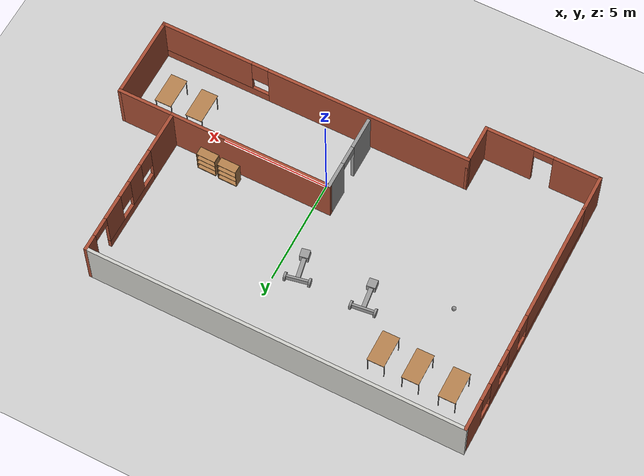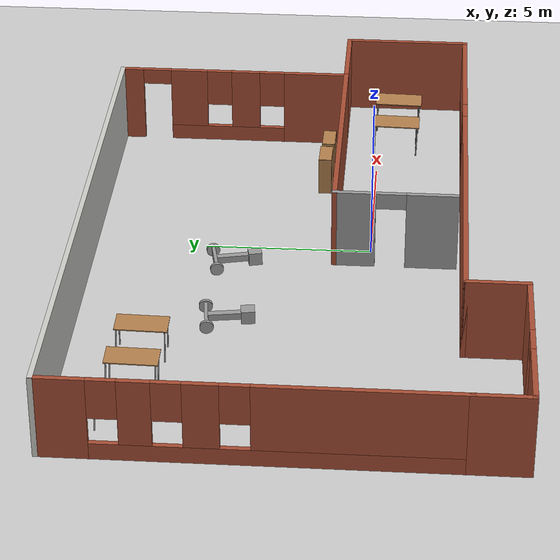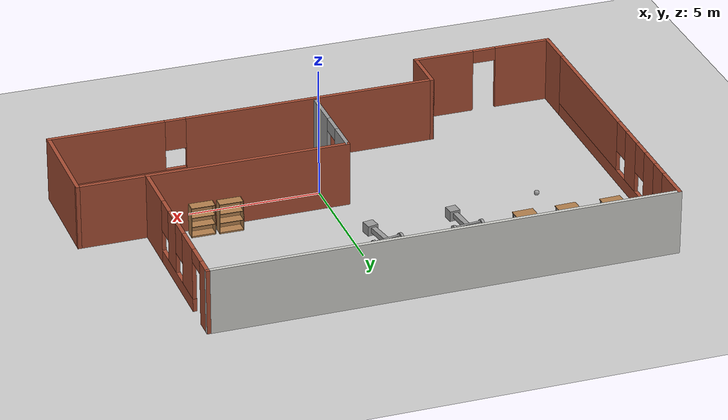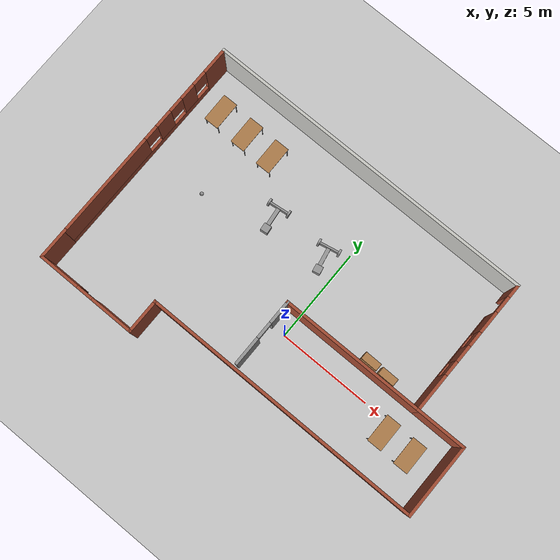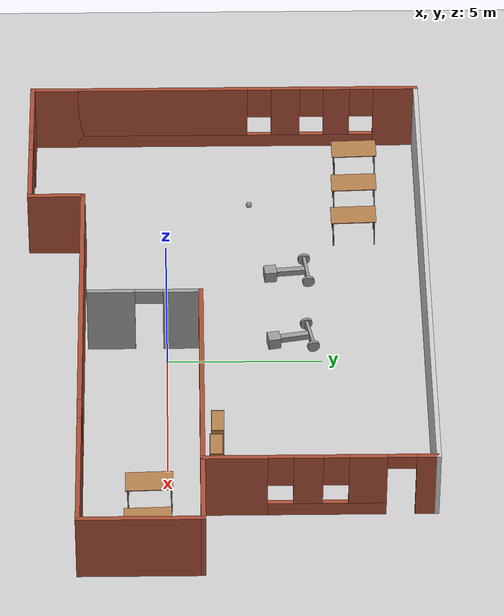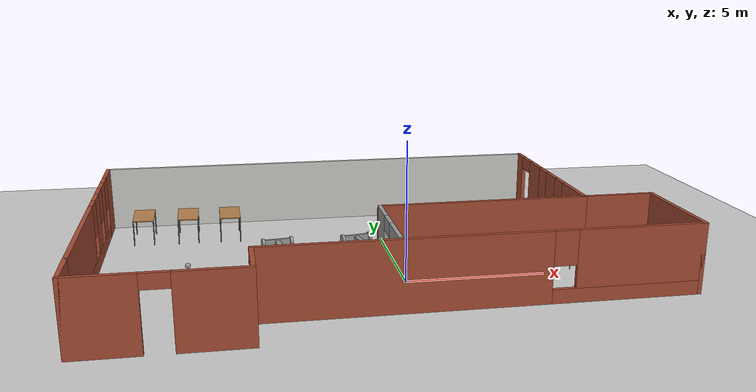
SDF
<sdf version="1.6">
 <world name="default">
  <plugin name="hello" filename="libhello.so"/>
  <light name="sun" type="directional">
   <pose>0 0 10 0 -0 0</pose>
   <diffuse>0.8 0.8 0.8 1</diffuse>
   <specular>0.2 0.2 0.2 1</specular>
   <attenuation>
    <range>1000</range>
    <constant>0.9</constant>
    <linear>0.01</linear>
    <quadratic>0.001</quadratic>
   </attenuation>
   <direction>-0.5 0.1 -0.9</direction>
  </light>
  <model name="ground_plane">
   <static>1</static>
   <link name="link">
    <collision name="collision">
     <geometry><plane><normal>0 0 1</normal><size>100 100</size></plane></geometry>
     <surface>
      <contact><collide_bitmask>65535</collide_bitmask></contact>
      <friction><ode><mu>100</mu><mu2>50</mu2></ode></friction>
     </surface>
    </collision>
    <visual name="visual">
     <cast_shadows>0</cast_shadows>
     <geometry><plane><normal>0 0 1</normal><size>100 100</size></plane></geometry>
     <material>
      <script><uri>file://media/materials/scripts/gazebo.material</uri><name>Gazebo/Grey</name></script>
     </material>
    </visual>
   </link>
  </model>
  <gravity>0 0 -9.8</gravity>
  <magnetic_field>6e-06 2.3e-05 -4.2e-05</magnetic_field>
  <atmosphere type="adiabatic"/>
  <physics name="default_physics" default="0" type="ode">
   <max_step_size>0.001</max_step_size>
   <real_time_factor>1</real_time_factor>
   <real_time_update_rate>1000</real_time_update_rate>
  </physics>
  <scene><ambient>0.4 0.4 0.4 1</ambient><background>0.7 0.7 0.7 1</background><shadows>1</shadows></scene>
  <spherical_coordinates>
   <surface_model>EARTH_WGS84</surface_model>
   <latitude_deg>0</latitude_deg>
   <longitude_deg>0</longitude_deg>
   <elevation>0</elevation>
   <heading_deg>0</heading_deg>
  </spherical_coordinates>
  <model name="model">
   <link name="link_0">
    <pose>-0.004 -0.004 -0.339991 0 -0 0</pose>
    <inertial>
     <mass>1</mass>
     <inertia>
      <ixx>0.166667</ixx>
      <ixy>0</ixy>
      <ixz>0</ixz>
      <iyy>0.166667</iyy>
      <iyz>0</iyz>
      <izz>0.166667</izz>
     </inertia>
    </inertial>
    <visual name="visual">
     <geometry><box><size>0.3 1 0.1</size></box></geometry>
     <material>
      <lighting>1</lighting>
      <script><uri>file://media/materials/scripts/gazebo.material</uri><name>Gazebo/Grey</name></script>
      <shader type="pixel"><normal_map>__default__</normal_map></shader>
      <ambient>0.3 0.3 0.3 1</ambient>
      <diffuse>0.7 0.7 0.7 1</diffuse>
      <specular>0.01 0.01 0.01 1</specular>
      <emissive>0 0 0 1</emissive>
     </material>
    </visual>
    <collision name="collision">
     <geometry><box><size>0.3 1 0.1</size></box></geometry>
     <surface>
      <friction>
       <ode><mu>1</mu><mu2>1</mu2><fdir1>0 0 0</fdir1><slip1>0</slip1><slip2>0</slip2></ode>
       <torsional>
        <coefficient>1</coefficient>
        <patch_radius>0</patch_radius>
        <surface_radius>0</surface_radius>
        <use_patch_radius>1</use_patch_radius>
        <ode><slip>0</slip></ode>
       </torsional>
      </friction>
      <bounce><restitution_coefficient>0</restitution_coefficient><threshold>1e+06</threshold></bounce>
      <contact>
       <collide_without_contact>0</collide_without_contact>
       <collide_without_contact_bitmask>1</collide_without_contact_bitmask>
       <collide_bitmask>1</collide_bitmask>
       <ode>
        <soft_cfm>0</soft_cfm>
        <soft_erp>0.2</soft_erp>
        <kp>1e+13</kp>
        <kd>1</kd>
        <max_vel>0.01</max_vel>
        <min_depth>0</min_depth>
       </ode>
       <bullet>
        <split_impulse>1</split_impulse>
        <split_impulse_penetration_threshold>-0.01</split_impulse_penetration_threshold>
        <soft_cfm>0</soft_cfm>
        <soft_erp>0.2</soft_erp>
        <kp>1e+13</kp>
        <kd>1</kd>
       </bullet>
      </contact>
     </surface>
    </collision>
   </link>
   <link name="link_2">
    <pose>-0.004 -0.554019 -0.340035 1.5707 -0 0</pose>
    <inertial>
     <mass>1</mass>
     <inertia><ixx>0.145833</ixx><ixy>0</ixy><ixz>0</ixz><iyy>0.145833</iyy><iyz>0</iyz><izz>0.125</izz></inertia>
    </inertial>
    <visual name="visual">
     <geometry><cylinder><radius>0.2</radius><length>0.1</length></cylinder></geometry>
     <material>
      <lighting>1</lighting>
      <script><uri>file://media/materials/scripts/gazebo.material</uri><name>Gazebo/Grey</name></script>
      <shader type="pixel"><normal_map>__default__</normal_map></shader>
      <ambient>0.3 0.3 0.3 1</ambient>
      <diffuse>0.7 0.7 0.7 1</diffuse>
      <specular>0.01 0.01 0.01 1</specular>
      <emissive>0 0 0 1</emissive>
     </material>
    </visual>
    <collision name="collision">
     <geometry><cylinder><radius>0.2</radius><length>0.1</length></cylinder></geometry>
     <surface>
      <friction>
       <ode><mu>1</mu><mu2>1</mu2><fdir1>0 0 0</fdir1><slip1>0</slip1><slip2>0</slip2></ode>
       <torsional>
        <coefficient>1</coefficient>
        <patch_radius>0</patch_radius>
        <surface_radius>0</surface_radius>
        <use_patch_radius>1</use_patch_radius>
        <ode><slip>0</slip></ode>
       </torsional>
      </friction>
      <bounce><restitution_coefficient>0</restitution_coefficient><threshold>1e+06</threshold></bounce>
      <contact>
       <collide_without_contact>0</collide_without_contact>
       <collide_without_contact_bitmask>1</collide_without_contact_bitmask>
       <collide_bitmask>1</collide_bitmask>
       <ode>
        <soft_cfm>0</soft_cfm>
        <soft_erp>0.2</soft_erp>
        <kp>1e+13</kp>
        <kd>1</kd>
        <max_vel>0.01</max_vel>
        <min_depth>0</min_depth>
       </ode>
       <bullet>
        <split_impulse>1</split_impulse>
        <split_impulse_penetration_threshold>-0.01</split_impulse_penetration_threshold>
        <soft_cfm>0</soft_cfm>
        <soft_erp>0.2</soft_erp>
        <kp>1e+13</kp>
        <kd>1</kd>
       </bullet>
      </contact>
     </surface>
    </collision>
   </link>
   <link name="link_2_clone">
    <pose>-0.004 0.546019 -0.339991 1.5707 -0 0</pose>
    <inertial>
     <mass>1</mass>
     <inertia><ixx>0.145833</ixx><ixy>0</ixy><ixz>0</ixz><iyy>0.145833</iyy><iyz>0</iyz><izz>0.125</izz></inertia>
    </inertial>
    <visual name="visual">
     <geometry><cylinder><radius>0.2</radius><length>0.1</length></cylinder></geometry>
     <material>
      <lighting>1</lighting>
      <script><uri>file://media/materials/scripts/gazebo.material</uri><name>Gazebo/Grey</name></script>
      <shader type="pixel"><normal_map>__default__</normal_map></shader>
      <ambient>0.3 0.3 0.3 1</ambient>
      <diffuse>0.7 0.7 0.7 1</diffuse>
      <specular>0.01 0.01 0.01 1</specular>
      <emissive>0 0 0 1</emissive>
     </material>
    </visual>
    <collision name="collision">
     <geometry><cylinder><radius>0.2</radius><length>0.1</length></cylinder></geometry>
     <surface>
      <friction>
       <ode><mu>1</mu><mu2>1</mu2><fdir1>0 0 0</fdir1><slip1>0</slip1><slip2>0</slip2></ode>
       <torsional>
        <coefficient>1</coefficient>
        <patch_radius>0</patch_radius>
        <surface_radius>0</surface_radius>
        <use_patch_radius>1</use_patch_radius>
        <ode><slip>0</slip></ode>
       </torsional>
      </friction>
      <bounce><restitution_coefficient>0</restitution_coefficient><threshold>1e+06</threshold></bounce>
      <contact>
       <collide_without_contact>0</collide_without_contact>
       <collide_without_contact_bitmask>1</collide_without_contact_bitmask>
       <collide_bitmask>1</collide_bitmask>
       <ode>
        <soft_cfm>0</soft_cfm>
        <soft_erp>0.2</soft_erp>
        <kp>1e+13</kp>
        <kd>1</kd>
        <max_vel>0.01</max_vel>
        <min_depth>0</min_depth>
       </ode>
       <bullet>
        <split_impulse>1</split_impulse>
        <split_impulse_penetration_threshold>-0.01</split_impulse_penetration_threshold>
        <soft_cfm>0</soft_cfm>
        <soft_erp>0.2</soft_erp>
        <kp>1e+13</kp>
        <kd>1</kd>
       </bullet>
      </contact>
     </surface>
    </collision>
   </link>
   <link name="link_3">
    <pose>-0.004 -0.004 0.160009 0 -0 0</pose>
    <inertial>
     <mass>1</mass>
     <inertia>
      <ixx>0.166667</ixx>
      <ixy>0</ixy>
      <ixz>0</ixz>
      <iyy>0.166667</iyy>
      <iyz>0</iyz>
      <izz>0.166667</izz>
     </inertia>
    </inertial>
    <visual name="visual">
     <geometry><box><size>0.2 0.2 1</size></box></geometry>
     <material>
      <lighting>1</lighting>
      <script><uri>file://media/materials/scripts/gazebo.material</uri><name>Gazebo/Grey</name></script>
      <shader type="pixel"><normal_map>__default__</normal_map></shader>
      <ambient>0.3 0.3 0.3 1</ambient>
      <diffuse>0.7 0.7 0.7 1</diffuse>
      <specular>0.01 0.01 0.01 1</specular>
      <emissive>0 0 0 1</emissive>
     </material>
    </visual>
    <collision name="collision">
     <geometry><box><size>0.2 0.2 1</size></box></geometry>
     <surface>
      <friction>
       <ode><mu>1</mu><mu2>1</mu2><fdir1>0 0 0</fdir1><slip1>0</slip1><slip2>0</slip2></ode>
       <torsional>
        <coefficient>1</coefficient>
        <patch_radius>0</patch_radius>
        <surface_radius>0</surface_radius>
        <use_patch_radius>1</use_patch_radius>
        <ode><slip>0</slip></ode>
       </torsional>
      </friction>
      <bounce><restitution_coefficient>0</restitution_coefficient><threshold>1e+06</threshold></bounce>
      <contact>
       <collide_without_contact>0</collide_without_contact>
       <collide_without_contact_bitmask>1</collide_without_contact_bitmask>
       <collide_bitmask>1</collide_bitmask>
       <ode>
        <soft_cfm>0</soft_cfm>
        <soft_erp>0.2</soft_erp>
        <kp>1e+13</kp>
        <kd>1</kd>
        <max_vel>0.01</max_vel>
        <min_depth>0</min_depth>
       </ode>
       <bullet>
        <split_impulse>1</split_impulse>
        <split_impulse_penetration_threshold>-0.01</split_impulse_penetration_threshold>
        <soft_cfm>0</soft_cfm>
        <soft_erp>0.2</soft_erp>
        <kp>1e+13</kp>
        <kd>1</kd>
       </bullet>
      </contact>
     </surface>
    </collision>
   </link>
   <link name="link_5">
    <pose>0.016 0.016 0.860009 0 -0 0</pose>
    <inertial>
     <mass>1</mass>
     <inertia>
      <ixx>0.166667</ixx>
      <ixy>0</ixy>
      <ixz>0</ixz>
      <iyy>0.166667</iyy>
      <iyz>0</iyz>
      <izz>0.166667</izz>
     </inertia>
    </inertial>
    <visual name="visual">
     <geometry><box><size>0.4 0.4 0.4</size></box></geometry>
     <material>
      <lighting>1</lighting>
      <script><uri>file://media/materials/scripts/gazebo.material</uri><name>Gazebo/Grey</name></script>
      <shader type="pixel"><normal_map>__default__</normal_map></shader>
      <ambient>0.3 0.3 0.3 1</ambient>
      <diffuse>0.7 0.7 0.7 1</diffuse>
      <specular>0.01 0.01 0.01 1</specular>
      <emissive>0 0 0 1</emissive>
     </material>
    </visual>
    <collision name="collision">
     <geometry><box><size>0.4 0.4 0.4</size></box></geometry>
     <surface>
      <friction>
       <ode><mu>1</mu><mu2>1</mu2><fdir1>0 0 0</fdir1><slip1>0</slip1><slip2>0</slip2></ode>
       <torsional>
        <coefficient>1</coefficient>
        <patch_radius>0</patch_radius>
        <surface_radius>0</surface_radius>
        <use_patch_radius>1</use_patch_radius>
        <ode><slip>0</slip></ode>
       </torsional>
      </friction>
      <bounce><restitution_coefficient>0</restitution_coefficient><threshold>1e+06</threshold></bounce>
      <contact>
       <collide_without_contact>0</collide_without_contact>
       <collide_without_contact_bitmask>1</collide_without_contact_bitmask>
       <collide_bitmask>1</collide_bitmask>
       <ode>
        <soft_cfm>0</soft_cfm>
        <soft_erp>0.2</soft_erp>
        <kp>1e+13</kp>
        <kd>1</kd>
        <max_vel>0.01</max_vel>
        <min_depth>0</min_depth>
       </ode>
       <bullet>
        <split_impulse>1</split_impulse>
        <split_impulse_penetration_threshold>-0.01</split_impulse_penetration_threshold>
        <soft_cfm>0</soft_cfm>
        <soft_erp>0.2</soft_erp>
        <kp>1e+13</kp>
        <kd>1</kd>
       </bullet>
      </contact>
     </surface>
    </collision>
   </link>
   <joint name="link_0_JOINT_0" type="revolute">
    <parent>link_0</parent>
    <child>link_2</child>
    <axis>
     <xyz>1 0 0</xyz>
     <use_parent_model_frame>0</use_parent_model_frame>
     <limit>
      <lower>-1.79769e+308</lower>
      <upper>1.79769e+308</upper>
      <effort>-1</effort>
      <velocity>-1</velocity>
     </limit>
     <dynamics>
      <spring_reference>0</spring_reference>
      <spring_stiffness>0</spring_stiffness>
      <damping>0</damping>
     </dynamics>
    </axis>
    <physics>
     <ode><limit><cfm>0</cfm><erp>0.2</erp></limit><suspension><cfm>0</cfm><erp>0.2</erp></suspension></ode>
    </physics>
   </joint>
   <joint name="link_0_JOINT_1" type="revolute">
    <parent>link_0</parent>
    <child>link_2_clone</child>
    <axis>
     <xyz>1 0 0</xyz>
     <use_parent_model_frame>0</use_parent_model_frame>
     <limit>
      <lower>-1.79769e+308</lower>
      <upper>1.79769e+308</upper>
      <effort>-1</effort>
      <velocity>-1</velocity>
     </limit>
     <dynamics>
      <spring_reference>0</spring_reference>
      <spring_stiffness>0</spring_stiffness>
      <damping>0</damping>
     </dynamics>
    </axis>
    <physics>
     <ode><limit><cfm>0</cfm><erp>0.2</erp></limit><suspension><cfm>0</cfm><erp>0.2</erp></suspension></ode>
    </physics>
   </joint>
   <joint name="link_3_JOINT_2" type="fixed">
    <parent>link_3</parent>
    <child>link_0</child>
    <physics>
     <ode><limit><cfm>0</cfm><erp>0.2</erp></limit><suspension><cfm>0</cfm><erp>0.2</erp></suspension></ode>
    </physics>
   </joint>
   <joint name="link_3_JOINT_5" type="revolute">
    <parent>link_3</parent>
    <child>link_5</child>
    <axis>
     <xyz>1 0 0</xyz>
     <use_parent_model_frame>0</use_parent_model_frame>
     <limit>
      <lower>-1.79769e+308</lower>
      <upper>1.79769e+308</upper>
      <effort>-1</effort>
      <velocity>-1</velocity>
     </limit>
     <dynamics>
      <spring_reference>0</spring_reference>
      <spring_stiffness>0</spring_stiffness>
      <damping>0</damping>
     </dynamics>
    </axis>
    <physics>
     <ode><limit><cfm>0</cfm><erp>0.2</erp></limit><suspension><cfm>0</cfm><erp>0.2</erp></suspension></ode>
    </physics>
   </joint>
   <static>0</static>
   <pose>-4.10983 4.24845 0.203394 -3.4e-05 1.54904 -1.45095</pose>
  </model>
  <model name="model_0">
   <pose>-0.6336 1.95139 0 0 -0 0</pose>
   <link name="Wall_10">
    <pose>7.50018 2.8 0 0 -0 1.57075</pose>
    <visual name="Wall_10_Visual_0">
     <pose>-2.68442 0 1.25 0 -0 0</pose>
     <geometry><box><size>2.09065 0.15 2.5</size></box></geometry>
     <material>
      <script><uri>file://media/materials/scripts/gazebo.material</uri><name>Gazebo/Bricks</name></script>
      <ambient>0.435294 0.796078 0.67451 1</ambient>
     </material>
     <meta><layer>0</layer></meta>
    </visual>
    <collision name="Wall_10_Collision_0">
     <geometry><box><size>2.09065 0.15 2.5</size></box></geometry>
     <pose>-2.68442 0 1.25 0 -0 0</pose>
    </collision>
    <visual name="Wall_10_Visual_1">
     <pose>3.35058 0 1.25 0 -0 0</pose>
     <geometry><box><size>0.758336 0.15 2.5</size></box></geometry>
     <material>
      <script><uri>file://media/materials/scripts/gazebo.material</uri><name>Gazebo/Bricks</name></script>
      <ambient>0.435294 0.796078 0.67451 1</ambient>
     </material>
     <meta><layer>0</layer></meta>
    </visual>
    <collision name="Wall_10_Collision_1">
     <geometry><box><size>0.758336 0.15 2.5</size></box></geometry>
     <pose>3.35058 0 1.25 0 -0 0</pose>
    </collision>
    <visual name="Wall_10_Visual_2">
     <pose>0.216155 0 0.25 0 -0 0</pose>
     <geometry><box><size>3.71051 0.15 0.5</size></box></geometry>
     <material>
      <script><uri>file://media/materials/scripts/gazebo.material</uri><name>Gazebo/Bricks</name></script>
      <ambient>0.435294 0.796078 0.67451 1</ambient>
     </material>
     <meta><layer>0</layer></meta>
    </visual>
    <collision name="Wall_10_Collision_2">
     <geometry><box><size>3.71051 0.15 0.5</size></box></geometry>
     <pose>0.216155 0 0.25 0 -0 0</pose>
    </collision>
    <visual name="Wall_10_Visual_3">
     <pose>-0.378984 0 1.5 0 -0 0</pose>
     <geometry><box><size>0.920234 0.15 2</size></box></geometry>
     <material>
      <script><uri>file://media/materials/scripts/gazebo.material</uri><name>Gazebo/Bricks</name></script>
      <ambient>0.435294 0.796078 0.67451 1</ambient>
     </material>
     <meta><layer>0</layer></meta>
    </visual>
    <collision name="Wall_10_Collision_3">
     <geometry><box><size>0.920234 0.15 2</size></box></geometry>
     <pose>-0.378984 0 1.5 0 -0 0</pose>
    </collision>
    <visual name="Wall_10_Visual_4">
     <pose>1.47627 0 1.5 0 -0 0</pose>
     <geometry><box><size>1.19028 0.15 2</size></box></geometry>
     <material>
      <script><uri>file://media/materials/scripts/gazebo.material</uri><name>Gazebo/Bricks</name></script>
      <ambient>0.435294 0.796078 0.67451 1</ambient>
     </material>
     <meta><layer>0</layer></meta>
    </visual>
    <collision name="Wall_10_Collision_4">
     <geometry><box><size>1.19028 0.15 2</size></box></geometry>
     <pose>1.47627 0 1.5 0 -0 0</pose>
    </collision>
    <visual name="Wall_10_Visual_5">
     <pose>-1.2391 0 1.9 0 -0 0</pose>
     <geometry><box><size>0.8 0.15 1.2</size></box></geometry>
     <material>
      <script><uri>file://media/materials/scripts/gazebo.material</uri><name>Gazebo/Bricks</name></script>
      <ambient>0.435294 0.796078 0.67451 1</ambient>
     </material>
     <meta><layer>0</layer></meta>
    </visual>
    <collision name="Wall_10_Collision_5">
     <geometry><box><size>0.8 0.15 1.2</size></box></geometry>
     <pose>-1.2391 0 1.9 0 -0 0</pose>
    </collision>
    <visual name="Wall_10_Visual_6">
     <pose>0.481133 0 1.9 0 -0 0</pose>
     <geometry><box><size>0.8 0.15 1.2</size></box></geometry>
     <material>
      <script><uri>file://media/materials/scripts/gazebo.material</uri><name>Gazebo/Bricks</name></script>
      <ambient>0.435294 0.796078 0.67451 1</ambient>
     </material>
     <meta><layer>0</layer></meta>
    </visual>
    <collision name="Wall_10_Collision_6">
     <geometry><box><size>0.8 0.15 1.2</size></box></geometry>
     <pose>0.481133 0 1.9 0 -0 0</pose>
    </collision>
    <visual name="Wall_10_Visual_7">
     <pose>2.52141 0 2.25 0 -0 0</pose>
     <geometry><box><size>0.9 0.15 0.5</size></box></geometry>
     <material>
      <script><uri>file://media/materials/scripts/gazebo.material</uri><name>Gazebo/Bricks</name></script>
      <ambient>0.435294 0.796078 0.67451 1</ambient>
     </material>
     <meta><layer>0</layer></meta>
    </visual>
    <collision name="Wall_10_Collision_7">
     <geometry><box><size>0.9 0.15 0.5</size></box></geometry>
     <pose>2.52141 0 2.25 0 -0 0</pose>
    </collision>
   </link>
   <link name="Wall_11">
    <collision name="Wall_11_Collision">
     <geometry><box><size>17.75 0.15 2.5</size></box></geometry>
     <pose>0 0 1.25 0 -0 0</pose>
    </collision>
    <visual name="Wall_11_Visual">
     <pose>0 0 1.25 0 -0 0</pose>
     <geometry><box><size>17.75 0.15 2.5</size></box></geometry>
     <material>
      <script><uri>file://media/materials/scripts/gazebo.material</uri><name>Gazebo/CeilingTiled</name></script>
      <ambient>0.435294 0.796078 0.67451 1</ambient>
     </material>
     <meta><layer>0</layer></meta>
    </visual>
    <pose>-1.29964 6.45474 0 0 -0 3.14159</pose>
   </link>
   <link name="Wall_12">
    <pose>-10.0998 0.799998 0 0 0 -1.57083</pose>
    <visual name="Wall_12_Visual_0">
     <pose>-4.98376 0 1.25 0 -0 0</pose>
     <geometry><box><size>1.49197 0.15 2.5</size></box></geometry>
     <material>
      <script><uri>file://media/materials/scripts/gazebo.material</uri><name>Gazebo/Bricks</name></script>
      <ambient>1 1 1 1</ambient>
     </material>
     <meta><layer>0</layer></meta>
    </visual>
    <collision name="Wall_12_Collision_0">
     <geometry><box><size>1.49197 0.15 2.5</size></box></geometry>
     <pose>-4.98376 0 1.25 0 -0 0</pose>
    </collision>
    <visual name="Wall_12_Visual_1">
     <pose>0.745985 0 0.25 0 -0 0</pose>
     <geometry><box><size>9.96752 0.15 0.5</size></box></geometry>
     <material>
      <script><uri>file://media/materials/scripts/gazebo.material</uri><name>Gazebo/Bricks</name></script>
      <ambient>1 1 1 1</ambient>
     </material>
     <meta><layer>0</layer></meta>
    </visual>
    <collision name="Wall_12_Collision_1">
     <geometry><box><size>9.96752 0.15 0.5</size></box></geometry>
     <pose>0.745985 0 0.25 0 -0 0</pose>
    </collision>
    <visual name="Wall_12_Visual_2">
     <pose>-2.99602 0 1.5 0 -0 0</pose>
     <geometry><box><size>0.88351 0.15 2</size></box></geometry>
     <material>
      <script><uri>file://media/materials/scripts/gazebo.material</uri><name>Gazebo/Bricks</name></script>
      <ambient>1 1 1 1</ambient>
     </material>
     <meta><layer>0</layer></meta>
    </visual>
    <collision name="Wall_12_Collision_2">
     <geometry><box><size>0.88351 0.15 2</size></box></geometry>
     <pose>-2.99602 0 1.5 0 -0 0</pose>
    </collision>
    <visual name="Wall_12_Visual_3">
     <pose>-1.27243 0 1.5 0 -0 0</pose>
     <geometry><box><size>0.963678 0.15 2</size></box></geometry>
     <material>
      <script><uri>file://media/materials/scripts/gazebo.material</uri><name>Gazebo/Bricks</name></script>
      <ambient>1 1 1 1</ambient>
     </material>
     <meta><layer>0</layer></meta>
    </visual>
    <collision name="Wall_12_Collision_3">
     <geometry><box><size>0.963678 0.15 2</size></box></geometry>
     <pose>-1.27243 0 1.5 0 -0 0</pose>
    </collision>
    <visual name="Wall_12_Visual_4">
     <pose>2.86958 0 1.5 0 -0 0</pose>
     <geometry><box><size>5.72034 0.15 2</size></box></geometry>
     <material>
      <script><uri>file://media/materials/scripts/gazebo.material</uri><name>Gazebo/Bricks</name></script>
      <ambient>1 1 1 1</ambient>
     </material>
     <meta><layer>0</layer></meta>
    </visual>
    <collision name="Wall_12_Collision_4">
     <geometry><box><size>5.72034 0.15 2</size></box></geometry>
     <pose>2.86958 0 1.5 0 -0 0</pose>
    </collision>
    <visual name="Wall_12_Visual_5">
     <pose>-3.83778 0 1.9 0 -0 0</pose>
     <geometry><box><size>0.8 0.15 1.2</size></box></geometry>
     <material>
      <script><uri>file://media/materials/scripts/gazebo.material</uri><name>Gazebo/Bricks</name></script>
      <ambient>1 1 1 1</ambient>
     </material>
     <meta><layer>0</layer></meta>
    </visual>
    <collision name="Wall_12_Collision_5">
     <geometry><box><size>0.8 0.15 1.2</size></box></geometry>
     <pose>-3.83778 0 1.9 0 -0 0</pose>
    </collision>
    <visual name="Wall_12_Visual_6">
     <pose>-2.15427 0 1.9 0 -0 0</pose>
     <geometry><box><size>0.8 0.15 1.2</size></box></geometry>
     <material>
      <script><uri>file://media/materials/scripts/gazebo.material</uri><name>Gazebo/Bricks</name></script>
      <ambient>1 1 1 1</ambient>
     </material>
     <meta><layer>0</layer></meta>
    </visual>
    <collision name="Wall_12_Collision_6">
     <geometry><box><size>0.8 0.15 1.2</size></box></geometry>
     <pose>-2.15427 0 1.9 0 -0 0</pose>
    </collision>
    <visual name="Wall_12_Visual_7">
     <pose>-0.390589 0 1.9 0 -0 0</pose>
     <geometry><box><size>0.8 0.15 1.2</size></box></geometry>
     <material>
      <script><uri>file://media/materials/scripts/gazebo.material</uri><name>Gazebo/Bricks</name></script>
      <ambient>1 1 1 1</ambient>
     </material>
     <meta><layer>0</layer></meta>
    </visual>
    <collision name="Wall_12_Collision_7">
     <geometry><box><size>0.8 0.15 1.2</size></box></geometry>
     <pose>-0.390589 0 1.9 0 -0 0</pose>
    </collision>
   </link>
   <link name="Wall_13">
    <collision name="Wall_13_Collision">
     <geometry><box><size>1.75 0.15 2.5</size></box></geometry>
     <pose>0 0 1.25 0 -0 0</pose>
    </collision>
    <visual name="Wall_13_Visual">
     <pose>0 0 1.25 0 -0 0</pose>
     <geometry><box><size>1.75 0.15 2.5</size></box></geometry>
     <material>
      <script><uri>file://media/materials/scripts/gazebo.material</uri><name>Gazebo/Bricks</name></script>
      <ambient>1 1 1 1</ambient>
     </material>
     <meta><layer>0</layer></meta>
    </visual>
    <pose>-10.1 -5.65475 0 0 0 -1.5708</pose>
   </link>
   <link name="Wall_14">
    <pose>-7.425 -6.45475 0 0 -0 0</pose>
    <visual name="Wall_14_Visual_0">
     <pose>-1.63288 0 1.25 0 -0 0</pose>
     <geometry><box><size>2.23424 0.15 2.5</size></box></geometry>
     <material>
      <script><uri>file://media/materials/scripts/gazebo.material</uri><name>Gazebo/Bricks</name></script>
      <ambient>1 1 1 1</ambient>
     </material>
     <meta><layer>0</layer></meta>
    </visual>
    <collision name="Wall_14_Collision_0">
     <geometry><box><size>2.23424 0.15 2.5</size></box></geometry>
     <pose>-1.63288 0 1.25 0 -0 0</pose>
    </collision>
    <visual name="Wall_14_Visual_1">
     <pose>1.56712 0 1.25 0 -0 0</pose>
     <geometry><box><size>2.36576 0.15 2.5</size></box></geometry>
     <material>
      <script><uri>file://media/materials/scripts/gazebo.material</uri><name>Gazebo/Bricks</name></script>
      <ambient>1 1 1 1</ambient>
     </material>
     <meta><layer>0</layer></meta>
    </visual>
    <collision name="Wall_14_Collision_1">
     <geometry><box><size>2.36576 0.15 2.5</size></box></geometry>
     <pose>1.56712 0 1.25 0 -0 0</pose>
    </collision>
    <visual name="Wall_14_Visual_2">
     <pose>-0.065763 0 2.25 0 -0 0</pose>
     <geometry><box><size>0.9 0.15 0.5</size></box></geometry>
     <material>
      <script><uri>file://media/materials/scripts/gazebo.material</uri><name>Gazebo/Bricks</name></script>
      <ambient>1 1 1 1</ambient>
     </material>
     <meta><layer>0</layer></meta>
    </visual>
    <collision name="Wall_14_Collision_2">
     <geometry><box><size>0.9 0.15 0.5</size></box></geometry>
     <pose>-0.065763 0 2.25 0 -0 0</pose>
    </collision>
   </link>
   <link name="Wall_15">
    <collision name="Wall_15_Collision">
     <geometry><box><size>1.9 0.15 2.5</size></box></geometry>
     <pose>0 0 1.25 0 -0 0</pose>
    </collision>
    <visual name="Wall_15_Visual">
     <pose>0 0 1.25 0 -0 0</pose>
     <geometry><box><size>1.9 0.15 2.5</size></box></geometry>
     <material>
      <script><uri>file://media/materials/scripts/gazebo.material</uri><name>Gazebo/Bricks</name></script>
      <ambient>1 1 1 1</ambient>
     </material>
     <meta><layer>0</layer></meta>
    </visual>
    <pose>-4.75 -5.57975 0 0 -0 1.5708</pose>
   </link>
   <link name="Wall_19">
    <collision name="Wall_19_Collision">
     <geometry><box><size>7.75 0.15 2.5</size></box></geometry>
     <pose>0 0 1.25 0 -0 0</pose>
    </collision>
    <visual name="Wall_19_Visual">
     <pose>0 0 1.25 0 -0 0</pose>
     <geometry><box><size>7.75 0.15 2.5</size></box></geometry>
     <material>
      <script><uri>file://media/materials/scripts/gazebo.material</uri><name>Gazebo/Bricks</name></script>
      <ambient>0.435294 0.796078 0.67451 1</ambient>
     </material>
     <meta><layer>0</layer></meta>
    </visual>
    <pose>3.7 -0.854748 0 0 -0 3.14159</pose>
   </link>
   <link name="Wall_20">
    <pose>-0.099999 -2.65475 0 0 0 -1.5708</pose>
    <visual name="Wall_20_Visual_0">
     <pose>-1.22543 0 1.25 0 -0 0</pose>
     <geometry><box><size>1.29914 0.15 2.5</size></box></geometry>
     <material>
      <script><uri>file://media/materials/scripts/gazebo.material</uri><name>Gazebo/Grey</name></script>
      <ambient>1 1 1 1</ambient>
     </material>
     <meta><layer>0</layer></meta>
    </visual>
    <collision name="Wall_20_Collision_0">
     <geometry><box><size>1.29914 0.15 2.5</size></box></geometry>
     <pose>-1.22543 0 1.25 0 -0 0</pose>
    </collision>
    <visual name="Wall_20_Visual_1">
     <pose>1.09957 0 1.25 0 -0 0</pose>
     <geometry><box><size>1.55086 0.15 2.5</size></box></geometry>
     <material>
      <script><uri>file://media/materials/scripts/gazebo.material</uri><name>Gazebo/Grey</name></script>
      <ambient>1 1 1 1</ambient>
     </material>
     <meta><layer>0</layer></meta>
    </visual>
    <collision name="Wall_20_Collision_1">
     <geometry><box><size>1.55086 0.15 2.5</size></box></geometry>
     <pose>1.09957 0 1.25 0 -0 0</pose>
    </collision>
    <visual name="Wall_20_Visual_2">
     <pose>-0.125864 0 2.25 0 -0 0</pose>
     <geometry><box><size>0.9 0.15 0.5</size></box></geometry>
     <material>
      <script><uri>file://media/materials/scripts/gazebo.material</uri><name>Gazebo/Grey</name></script>
      <ambient>1 1 1 1</ambient>
     </material>
     <meta><layer>0</layer></meta>
    </visual>
    <collision name="Wall_20_Collision_2">
     <geometry><box><size>0.9 0.15 0.5</size></box></geometry>
     <pose>-0.125864 0 2.25 0 -0 0</pose>
    </collision>
   </link>
   <link name="Wall_7">
    <pose>2.675 -4.70475 0 0 -0 0</pose>
    <visual name="Wall_7_Visual_0">
     <pose>-2.63677 0 1.25 0 -0 0</pose>
     <geometry><box><size>9.72647 0.15 2.5</size></box></geometry>
     <material>
      <script><uri>file://media/materials/scripts/gazebo.material</uri><name>Gazebo/Bricks</name></script>
      <ambient>0.435294 0.796078 0.67451 1</ambient>
     </material>
     <meta><layer>0</layer></meta>
    </visual>
    <collision name="Wall_7_Collision_0">
     <geometry><box><size>9.72647 0.15 2.5</size></box></geometry>
     <pose>-2.63677 0 1.25 0 -0 0</pose>
    </collision>
    <visual name="Wall_7_Visual_1">
     <pose>4.86323 0 0.25 0 -0 0</pose>
     <geometry><box><size>5.27353 0.15 0.5</size></box></geometry>
     <material>
      <script><uri>file://media/materials/scripts/gazebo.material</uri><name>Gazebo/Bricks</name></script>
      <ambient>0.435294 0.796078 0.67451 1</ambient>
     </material>
     <meta><layer>0</layer></meta>
    </visual>
    <collision name="Wall_7_Collision_1">
     <geometry><box><size>5.27353 0.15 0.5</size></box></geometry>
     <pose>4.86323 0 0.25 0 -0 0</pose>
    </collision>
    <visual name="Wall_7_Visual_2">
     <pose>5.26323 0 1.5 0 -0 0</pose>
     <geometry><box><size>4.47353 0.15 2</size></box></geometry>
     <material>
      <script><uri>file://media/materials/scripts/gazebo.material</uri><name>Gazebo/Bricks</name></script>
      <ambient>0.435294 0.796078 0.67451 1</ambient>
     </material>
     <meta><layer>0</layer></meta>
    </visual>
    <collision name="Wall_7_Collision_2">
     <geometry><box><size>4.47353 0.15 2</size></box></geometry>
     <pose>5.26323 0 1.5 0 -0 0</pose>
    </collision>
    <visual name="Wall_7_Visual_3">
     <pose>2.62647 0 1.9 0 -0 0</pose>
     <geometry><box><size>0.8 0.15 1.2</size></box></geometry>
     <material>
      <script><uri>file://media/materials/scripts/gazebo.material</uri><name>Gazebo/Bricks</name></script>
      <ambient>0.435294 0.796078 0.67451 1</ambient>
     </material>
     <meta><layer>0</layer></meta>
    </visual>
    <collision name="Wall_7_Collision_3">
     <geometry><box><size>0.8 0.15 1.2</size></box></geometry>
     <pose>2.62647 0 1.9 0 -0 0</pose>
    </collision>
   </link>
   <link name="Wall_8">
    <collision name="Wall_8_Collision">
     <geometry><box><size>4 0.15 2.5</size></box></geometry>
     <pose>0 0 1.25 0 -0 0</pose>
    </collision>
    <visual name="Wall_8_Visual">
     <pose>0 0 1.25 0 -0 0</pose>
     <geometry><box><size>4 0.15 2.5</size></box></geometry>
     <material>
      <script><uri>file://media/materials/scripts/gazebo.material</uri><name>Gazebo/Bricks</name></script>
      <ambient>1 1 1 1</ambient>
     </material>
     <meta><layer>0</layer></meta>
    </visual>
    <pose>10.1 -2.77975 0 0 -0 1.5708</pose>
   </link>
   <link name="Wall_9">
    <collision name="Wall_9_Collision">
     <geometry><box><size>2.75 0.15 2.5</size></box></geometry>
     <pose>0 0 1.25 0 -0 0</pose>
    </collision>
    <visual name="Wall_9_Visual">
     <pose>0 0 1.25 0 -0 0</pose>
     <geometry><box><size>2.75 0.15 2.5</size></box></geometry>
     <material>
      <script><uri>file://media/materials/scripts/gazebo.material</uri><name>Gazebo/Bricks</name></script>
      <ambient>1 1 1 1</ambient>
     </material>
     <meta><layer>0</layer></meta>
    </visual>
    <pose>8.8 -0.854748 0 0 -0 3.14159</pose>
   </link>
   <static>1</static>
  </model>
  <model name="bookshelf">
   <static>1</static>
   <link name="link">
    <inertial><mass>1</mass></inertial>
    <collision name="back">
     <pose>0 0.005 0.6 0 -0 0</pose>
     <geometry><box><size>0.9 0.01 1.2</size></box></geometry>
    </collision>
    <visual name="visual1">
     <pose>0 0.005 0.6 0 -0 0</pose>
     <geometry><box><size>0.9 0.01 1.2</size></box></geometry>
     <material>
      <script><uri>file://media/materials/scripts/gazebo.material</uri><name>Gazebo/Wood</name></script>
     </material>
    </visual>
    <collision name="left_side">
     <pose>0.45 -0.195 0.6 0 -0 0</pose>
     <geometry><box><size>0.02 0.4 1.2</size></box></geometry>
    </collision>
    <visual name="visual2">
     <pose>0.45 -0.195 0.6 0 -0 0</pose>
     <geometry><box><size>0.02 0.4 1.2</size></box></geometry>
     <material>
      <script><uri>file://media/materials/scripts/gazebo.material</uri><name>Gazebo/Wood</name></script>
     </material>
    </visual>
    <collision name="right_side">
     <pose>-0.45 -0.195 0.6 0 -0 0</pose>
     <geometry><box><size>0.02 0.4 1.2</size></box></geometry>
    </collision>
    <visual name="visual3">
     <pose>-0.45 -0.195 0.6 0 -0 0</pose>
     <geometry><box><size>0.02 0.4 1.2</size></box></geometry>
     <material>
      <script><uri>file://media/materials/scripts/gazebo.material</uri><name>Gazebo/Wood</name></script>
     </material>
    </visual>
    <collision name="bottom">
     <pose>0 -0.195 0.03 0 -0 0</pose>
     <geometry><box><size>0.88 0.4 0.06</size></box></geometry>
    </collision>
    <visual name="visual4">
     <pose>0 -0.195 0.03 0 -0 0</pose>
     <geometry><box><size>0.88 0.4 0.06</size></box></geometry>
     <material>
      <script><uri>file://media/materials/scripts/gazebo.material</uri><name>Gazebo/Wood</name></script>
     </material>
    </visual>
    <collision name="top">
     <pose>0 -0.195 1.19 0 -0 0</pose>
     <geometry><box><size>0.88 0.4 0.02</size></box></geometry>
    </collision>
    <visual name="visual5">
     <pose>0 -0.195 1.19 0 -0 0</pose>
     <geometry><box><size>0.88 0.4 0.02</size></box></geometry>
     <material>
      <script><uri>file://media/materials/scripts/gazebo.material</uri><name>Gazebo/Wood</name></script>
     </material>
    </visual>
    <collision name="low_shelf">
     <pose>0 -0.195 0.43 0 -0 0</pose>
     <geometry><box><size>0.88 0.4 0.02</size></box></geometry>
    </collision>
    <visual name="visual6">
     <pose>0 -0.195 0.43 0 -0 0</pose>
     <geometry><box><size>0.88 0.4 0.02</size></box></geometry>
     <material>
      <script><uri>file://media/materials/scripts/gazebo.material</uri><name>Gazebo/Wood</name></script>
     </material>
    </visual>
    <collision name="high_shelf">
     <pose>0 -0.195 0.8 0 -0 0</pose>
     <geometry><box><size>0.88 0.4 0.02</size></box></geometry>
    </collision>
    <visual name="visual7">
     <pose>0 -0.195 0.8 0 -0 0</pose>
     <geometry><box><size>0.88 0.4 0.02</size></box></geometry>
     <material>
      <script><uri>file://media/materials/scripts/gazebo.material</uri><name>Gazebo/Wood</name></script>
     </material>
    </visual>
   </link>
   <pose>4.97014 1.33847 0 0 -0 3.13189</pose>
  </model>
  <model name="bookshelf_clone">
   <static>1</static>
   <link name="link">
    <inertial><mass>1</mass></inertial>
    <collision name="back">
     <pose>0 0.005 0.6 0 -0 0</pose>
     <geometry><box><size>0.9 0.01 1.2</size></box></geometry>
    </collision>
    <visual name="visual1">
     <pose>0 0.005 0.6 0 -0 0</pose>
     <geometry><box><size>0.9 0.01 1.2</size></box></geometry>
     <material>
      <script><uri>file://media/materials/scripts/gazebo.material</uri><name>Gazebo/Wood</name></script>
     </material>
    </visual>
    <collision name="left_side">
     <pose>0.45 -0.195 0.6 0 -0 0</pose>
     <geometry><box><size>0.02 0.4 1.2</size></box></geometry>
    </collision>
    <visual name="visual2">
     <pose>0.45 -0.195 0.6 0 -0 0</pose>
     <geometry><box><size>0.02 0.4 1.2</size></box></geometry>
     <material>
      <script><uri>file://media/materials/scripts/gazebo.material</uri><name>Gazebo/Wood</name></script>
     </material>
    </visual>
    <collision name="right_side">
     <pose>-0.45 -0.195 0.6 0 -0 0</pose>
     <geometry><box><size>0.02 0.4 1.2</size></box></geometry>
    </collision>
    <visual name="visual3">
     <pose>-0.45 -0.195 0.6 0 -0 0</pose>
     <geometry><box><size>0.02 0.4 1.2</size></box></geometry>
     <material>
      <script><uri>file://media/materials/scripts/gazebo.material</uri><name>Gazebo/Wood</name></script>
     </material>
    </visual>
    <collision name="bottom">
     <pose>0 -0.195 0.03 0 -0 0</pose>
     <geometry><box><size>0.88 0.4 0.06</size></box></geometry>
    </collision>
    <visual name="visual4">
     <pose>0 -0.195 0.03 0 -0 0</pose>
     <geometry><box><size>0.88 0.4 0.06</size></box></geometry>
     <material>
      <script><uri>file://media/materials/scripts/gazebo.material</uri><name>Gazebo/Wood</name></script>
     </material>
    </visual>
    <collision name="top">
     <pose>0 -0.195 1.19 0 -0 0</pose>
     <geometry><box><size>0.88 0.4 0.02</size></box></geometry>
    </collision>
    <visual name="visual5">
     <pose>0 -0.195 1.19 0 -0 0</pose>
     <geometry><box><size>0.88 0.4 0.02</size></box></geometry>
     <material>
      <script><uri>file://media/materials/scripts/gazebo.material</uri><name>Gazebo/Wood</name></script>
     </material>
    </visual>
    <collision name="low_shelf">
     <pose>0 -0.195 0.43 0 -0 0</pose>
     <geometry><box><size>0.88 0.4 0.02</size></box></geometry>
    </collision>
    <visual name="visual6">
     <pose>0 -0.195 0.43 0 -0 0</pose>
     <geometry><box><size>0.88 0.4 0.02</size></box></geometry>
     <material>
      <script><uri>file://media/materials/scripts/gazebo.material</uri><name>Gazebo/Wood</name></script>
     </material>
    </visual>
    <collision name="high_shelf">
     <pose>0 -0.195 0.8 0 -0 0</pose>
     <geometry><box><size>0.88 0.4 0.02</size></box></geometry>
    </collision>
    <visual name="visual7">
     <pose>0 -0.195 0.8 0 -0 0</pose>
     <geometry><box><size>0.88 0.4 0.02</size></box></geometry>
     <material>
      <script><uri>file://media/materials/scripts/gazebo.material</uri><name>Gazebo/Wood</name></script>
     </material>
    </visual>
   </link>
   <pose>3.92518 1.39004 0 0 -0 3.13189</pose>
  </model>
  <model name="model_clone">
   <link name="link_0">
    <pose>-0.004 -0.004 -0.339991 0 -0 0</pose>
    <inertial>
     <mass>1</mass>
     <inertia>
      <ixx>0.166667</ixx>
      <ixy>0</ixy>
      <ixz>0</ixz>
      <iyy>0.166667</iyy>
      <iyz>0</iyz>
      <izz>0.166667</izz>
     </inertia>
    </inertial>
    <visual name="visual">
     <geometry><box><size>0.3 1 0.1</size></box></geometry>
     <material>
      <lighting>1</lighting>
      <script><uri>file://media/materials/scripts/gazebo.material</uri><name>Gazebo/Grey</name></script>
      <shader type="pixel"><normal_map>__default__</normal_map></shader>
      <ambient>0.3 0.3 0.3 1</ambient>
      <diffuse>0.7 0.7 0.7 1</diffuse>
      <specular>0.01 0.01 0.01 1</specular>
      <emissive>0 0 0 1</emissive>
     </material>
    </visual>
    <collision name="collision">
     <geometry><box><size>0.3 1 0.1</size></box></geometry>
     <surface>
      <friction>
       <ode><mu>1</mu><mu2>1</mu2><fdir1>0 0 0</fdir1><slip1>0</slip1><slip2>0</slip2></ode>
       <torsional>
        <coefficient>1</coefficient>
        <patch_radius>0</patch_radius>
        <surface_radius>0</surface_radius>
        <use_patch_radius>1</use_patch_radius>
        <ode><slip>0</slip></ode>
       </torsional>
      </friction>
      <bounce><restitution_coefficient>0</restitution_coefficient><threshold>1e+06</threshold></bounce>
      <contact>
       <collide_without_contact>0</collide_without_contact>
       <collide_without_contact_bitmask>1</collide_without_contact_bitmask>
       <collide_bitmask>1</collide_bitmask>
       <ode>
        <soft_cfm>0</soft_cfm>
        <soft_erp>0.2</soft_erp>
        <kp>1e+13</kp>
        <kd>1</kd>
        <max_vel>0.01</max_vel>
        <min_depth>0</min_depth>
       </ode>
       <bullet>
        <split_impulse>1</split_impulse>
        <split_impulse_penetration_threshold>-0.01</split_impulse_penetration_threshold>
        <soft_cfm>0</soft_cfm>
        <soft_erp>0.2</soft_erp>
        <kp>1e+13</kp>
        <kd>1</kd>
       </bullet>
      </contact>
     </surface>
    </collision>
   </link>
   <link name="link_2">
    <pose>-0.004 -0.554019 -0.340035 1.5707 -0 0</pose>
    <inertial>
     <mass>1</mass>
     <inertia><ixx>0.145833</ixx><ixy>0</ixy><ixz>0</ixz><iyy>0.145833</iyy><iyz>0</iyz><izz>0.125</izz></inertia>
    </inertial>
    <visual name="visual">
     <geometry><cylinder><radius>0.2</radius><length>0.1</length></cylinder></geometry>
     <material>
      <lighting>1</lighting>
      <script><uri>file://media/materials/scripts/gazebo.material</uri><name>Gazebo/Grey</name></script>
      <shader type="pixel"><normal_map>__default__</normal_map></shader>
      <ambient>0.3 0.3 0.3 1</ambient>
      <diffuse>0.7 0.7 0.7 1</diffuse>
      <specular>0.01 0.01 0.01 1</specular>
      <emissive>0 0 0 1</emissive>
     </material>
    </visual>
    <collision name="collision">
     <geometry><cylinder><radius>0.2</radius><length>0.1</length></cylinder></geometry>
     <surface>
      <friction>
       <ode><mu>1</mu><mu2>1</mu2><fdir1>0 0 0</fdir1><slip1>0</slip1><slip2>0</slip2></ode>
       <torsional>
        <coefficient>1</coefficient>
        <patch_radius>0</patch_radius>
        <surface_radius>0</surface_radius>
        <use_patch_radius>1</use_patch_radius>
        <ode><slip>0</slip></ode>
       </torsional>
      </friction>
      <bounce><restitution_coefficient>0</restitution_coefficient><threshold>1e+06</threshold></bounce>
      <contact>
       <collide_without_contact>0</collide_without_contact>
       <collide_without_contact_bitmask>1</collide_without_contact_bitmask>
       <collide_bitmask>1</collide_bitmask>
       <ode>
        <soft_cfm>0</soft_cfm>
        <soft_erp>0.2</soft_erp>
        <kp>1e+13</kp>
        <kd>1</kd>
        <max_vel>0.01</max_vel>
        <min_depth>0</min_depth>
       </ode>
       <bullet>
        <split_impulse>1</split_impulse>
        <split_impulse_penetration_threshold>-0.01</split_impulse_penetration_threshold>
        <soft_cfm>0</soft_cfm>
        <soft_erp>0.2</soft_erp>
        <kp>1e+13</kp>
        <kd>1</kd>
       </bullet>
      </contact>
     </surface>
    </collision>
   </link>
   <link name="link_2_clone">
    <pose>-0.004 0.546019 -0.339991 1.5707 -0 0</pose>
    <inertial>
     <mass>1</mass>
     <inertia><ixx>0.145833</ixx><ixy>0</ixy><ixz>0</ixz><iyy>0.145833</iyy><iyz>0</iyz><izz>0.125</izz></inertia>
    </inertial>
    <visual name="visual">
     <geometry><cylinder><radius>0.2</radius><length>0.1</length></cylinder></geometry>
     <material>
      <lighting>1</lighting>
      <script><uri>file://media/materials/scripts/gazebo.material</uri><name>Gazebo/Grey</name></script>
      <shader type="pixel"><normal_map>__default__</normal_map></shader>
      <ambient>0.3 0.3 0.3 1</ambient>
      <diffuse>0.7 0.7 0.7 1</diffuse>
      <specular>0.01 0.01 0.01 1</specular>
      <emissive>0 0 0 1</emissive>
     </material>
    </visual>
    <collision name="collision">
     <geometry><cylinder><radius>0.2</radius><length>0.1</length></cylinder></geometry>
     <surface>
      <friction>
       <ode><mu>1</mu><mu2>1</mu2><fdir1>0 0 0</fdir1><slip1>0</slip1><slip2>0</slip2></ode>
       <torsional>
        <coefficient>1</coefficient>
        <patch_radius>0</patch_radius>
        <surface_radius>0</surface_radius>
        <use_patch_radius>1</use_patch_radius>
        <ode><slip>0</slip></ode>
       </torsional>
      </friction>
      <bounce><restitution_coefficient>0</restitution_coefficient><threshold>1e+06</threshold></bounce>
      <contact>
       <collide_without_contact>0</collide_without_contact>
       <collide_without_contact_bitmask>1</collide_without_contact_bitmask>
       <collide_bitmask>1</collide_bitmask>
       <ode>
        <soft_cfm>0</soft_cfm>
        <soft_erp>0.2</soft_erp>
        <kp>1e+13</kp>
        <kd>1</kd>
        <max_vel>0.01</max_vel>
        <min_depth>0</min_depth>
       </ode>
       <bullet>
        <split_impulse>1</split_impulse>
        <split_impulse_penetration_threshold>-0.01</split_impulse_penetration_threshold>
        <soft_cfm>0</soft_cfm>
        <soft_erp>0.2</soft_erp>
        <kp>1e+13</kp>
        <kd>1</kd>
       </bullet>
      </contact>
     </surface>
    </collision>
   </link>
   <link name="link_3">
    <pose>-0.004 -0.004 0.160009 0 -0 0</pose>
    <inertial>
     <mass>1</mass>
     <inertia>
      <ixx>0.166667</ixx>
      <ixy>0</ixy>
      <ixz>0</ixz>
      <iyy>0.166667</iyy>
      <iyz>0</iyz>
      <izz>0.166667</izz>
     </inertia>
    </inertial>
    <visual name="visual">
     <geometry><box><size>0.2 0.2 1</size></box></geometry>
     <material>
      <lighting>1</lighting>
      <script><uri>file://media/materials/scripts/gazebo.material</uri><name>Gazebo/Grey</name></script>
      <shader type="pixel"><normal_map>__default__</normal_map></shader>
      <ambient>0.3 0.3 0.3 1</ambient>
      <diffuse>0.7 0.7 0.7 1</diffuse>
      <specular>0.01 0.01 0.01 1</specular>
      <emissive>0 0 0 1</emissive>
     </material>
    </visual>
    <collision name="collision">
     <geometry><box><size>0.2 0.2 1</size></box></geometry>
     <surface>
      <friction>
       <ode><mu>1</mu><mu2>1</mu2><fdir1>0 0 0</fdir1><slip1>0</slip1><slip2>0</slip2></ode>
       <torsional>
        <coefficient>1</coefficient>
        <patch_radius>0</patch_radius>
        <surface_radius>0</surface_radius>
        <use_patch_radius>1</use_patch_radius>
        <ode><slip>0</slip></ode>
       </torsional>
      </friction>
      <bounce><restitution_coefficient>0</restitution_coefficient><threshold>1e+06</threshold></bounce>
      <contact>
       <collide_without_contact>0</collide_without_contact>
       <collide_without_contact_bitmask>1</collide_without_contact_bitmask>
       <collide_bitmask>1</collide_bitmask>
       <ode>
        <soft_cfm>0</soft_cfm>
        <soft_erp>0.2</soft_erp>
        <kp>1e+13</kp>
        <kd>1</kd>
        <max_vel>0.01</max_vel>
        <min_depth>0</min_depth>
       </ode>
       <bullet>
        <split_impulse>1</split_impulse>
        <split_impulse_penetration_threshold>-0.01</split_impulse_penetration_threshold>
        <soft_cfm>0</soft_cfm>
        <soft_erp>0.2</soft_erp>
        <kp>1e+13</kp>
        <kd>1</kd>
       </bullet>
      </contact>
     </surface>
    </collision>
   </link>
   <link name="link_5">
    <pose>0.016 0.016 0.860009 0 -0 0</pose>
    <inertial>
     <mass>1</mass>
     <inertia>
      <ixx>0.166667</ixx>
      <ixy>0</ixy>
      <ixz>0</ixz>
      <iyy>0.166667</iyy>
      <iyz>0</iyz>
      <izz>0.166667</izz>
     </inertia>
    </inertial>
    <visual name="visual">
     <geometry><box><size>0.4 0.4 0.4</size></box></geometry>
     <material>
      <lighting>1</lighting>
      <script><uri>file://media/materials/scripts/gazebo.material</uri><name>Gazebo/Grey</name></script>
      <shader type="pixel"><normal_map>__default__</normal_map></shader>
      <ambient>0.3 0.3 0.3 1</ambient>
      <diffuse>0.7 0.7 0.7 1</diffuse>
      <specular>0.01 0.01 0.01 1</specular>
      <emissive>0 0 0 1</emissive>
     </material>
    </visual>
    <collision name="collision">
     <geometry><box><size>0.4 0.4 0.4</size></box></geometry>
     <surface>
      <friction>
       <ode><mu>1</mu><mu2>1</mu2><fdir1>0 0 0</fdir1><slip1>0</slip1><slip2>0</slip2></ode>
       <torsional>
        <coefficient>1</coefficient>
        <patch_radius>0</patch_radius>
        <surface_radius>0</surface_radius>
        <use_patch_radius>1</use_patch_radius>
        <ode><slip>0</slip></ode>
       </torsional>
      </friction>
      <bounce><restitution_coefficient>0</restitution_coefficient><threshold>1e+06</threshold></bounce>
      <contact>
       <collide_without_contact>0</collide_without_contact>
       <collide_without_contact_bitmask>1</collide_without_contact_bitmask>
       <collide_bitmask>1</collide_bitmask>
       <ode>
        <soft_cfm>0</soft_cfm>
        <soft_erp>0.2</soft_erp>
        <kp>1e+13</kp>
        <kd>1</kd>
        <max_vel>0.01</max_vel>
        <min_depth>0</min_depth>
       </ode>
       <bullet>
        <split_impulse>1</split_impulse>
        <split_impulse_penetration_threshold>-0.01</split_impulse_penetration_threshold>
        <soft_cfm>0</soft_cfm>
        <soft_erp>0.2</soft_erp>
        <kp>1e+13</kp>
        <kd>1</kd>
       </bullet>
      </contact>
     </surface>
    </collision>
   </link>
   <joint name="link_0_JOINT_0" type="revolute">
    <parent>link_0</parent>
    <child>link_2</child>
    <axis>
     <xyz>1 0 0</xyz>
     <use_parent_model_frame>0</use_parent_model_frame>
     <limit>
      <lower>-1.79769e+308</lower>
      <upper>1.79769e+308</upper>
      <effort>-1</effort>
      <velocity>-1</velocity>
     </limit>
     <dynamics>
      <spring_reference>0</spring_reference>
      <spring_stiffness>0</spring_stiffness>
      <damping>0</damping>
     </dynamics>
    </axis>
    <physics>
     <ode><limit><cfm>0</cfm><erp>0.2</erp></limit><suspension><cfm>0</cfm><erp>0.2</erp></suspension></ode>
    </physics>
   </joint>
   <joint name="link_0_JOINT_1" type="revolute">
    <parent>link_0</parent>
    <child>link_2_clone</child>
    <axis>
     <xyz>1 0 0</xyz>
     <use_parent_model_frame>0</use_parent_model_frame>
     <limit>
      <lower>-1.79769e+308</lower>
      <upper>1.79769e+308</upper>
      <effort>-1</effort>
      <velocity>-1</velocity>
     </limit>
     <dynamics>
      <spring_reference>0</spring_reference>
      <spring_stiffness>0</spring_stiffness>
      <damping>0</damping>
     </dynamics>
    </axis>
    <physics>
     <ode><limit><cfm>0</cfm><erp>0.2</erp></limit><suspension><cfm>0</cfm><erp>0.2</erp></suspension></ode>
    </physics>
   </joint>
   <joint name="link_3_JOINT_2" type="fixed">
    <parent>link_3</parent>
    <child>link_0</child>
    <physics>
     <ode><limit><cfm>0</cfm><erp>0.2</erp></limit><suspension><cfm>0</cfm><erp>0.2</erp></suspension></ode>
    </physics>
   </joint>
   <joint name="link_3_JOINT_5" type="revolute">
    <parent>link_3</parent>
    <child>link_5</child>
    <axis>
     <xyz>1 0 0</xyz>
     <use_parent_model_frame>0</use_parent_model_frame>
     <limit>
      <lower>-1.79769e+308</lower>
      <upper>1.79769e+308</upper>
      <effort>-1</effort>
      <velocity>-1</velocity>
     </limit>
     <dynamics>
      <spring_reference>0</spring_reference>
      <spring_stiffness>0</spring_stiffness>
      <damping>0</damping>
     </dynamics>
    </axis>
    <physics>
     <ode><limit><cfm>0</cfm><erp>0.2</erp></limit><suspension><cfm>0</cfm><erp>0.2</erp></suspension></ode>
    </physics>
   </joint>
   <static>0</static>
   <pose>-0.978271 4.30124 0.202786 -6.9e-05 1.55084 -1.37401</pose>
  </model>
  <model name="table">
   <static>1</static>
   <link name="link">
    <collision name="surface">
     <pose>0 0 1 0 -0 0</pose>
     <geometry><box><size>1.5 0.8 0.03</size></box></geometry>
     <surface><friction><ode><mu>0.6</mu><mu2>0.6</mu2></ode></friction></surface>
    </collision>
    <visual name="visual1">
     <pose>0 0 1 0 -0 0</pose>
     <geometry><box><size>1.5 0.8 0.03</size></box></geometry>
     <material>
      <script><uri>file://media/materials/scripts/gazebo.material</uri><name>Gazebo/Wood</name></script>
     </material>
    </visual>
    <collision name="front_left_leg">
     <pose>0.68 0.38 0.5 0 -0 0</pose>
     <geometry><cylinder><radius>0.02</radius><length>1</length></cylinder></geometry>
    </collision>
    <visual name="front_left_leg">
     <pose>0.68 0.38 0.5 0 -0 0</pose>
     <geometry><cylinder><radius>0.02</radius><length>1</length></cylinder></geometry>
     <material>
      <script><uri>file://media/materials/scripts/gazebo.material</uri><name>Gazebo/Grey</name></script>
     </material>
    </visual>
    <collision name="front_right_leg">
     <pose>0.68 -0.38 0.5 0 -0 0</pose>
     <geometry><cylinder><radius>0.02</radius><length>1</length></cylinder></geometry>
    </collision>
    <visual name="front_right_leg">
     <pose>0.68 -0.38 0.5 0 -0 0</pose>
     <geometry><cylinder><radius>0.02</radius><length>1</length></cylinder></geometry>
     <material>
      <script><uri>file://media/materials/scripts/gazebo.material</uri><name>Gazebo/Grey</name></script>
     </material>
    </visual>
    <collision name="back_right_leg">
     <pose>-0.68 -0.38 0.5 0 -0 0</pose>
     <geometry><cylinder><radius>0.02</radius><length>1</length></cylinder></geometry>
    </collision>
    <visual name="back_right_leg">
     <pose>-0.68 -0.38 0.5 0 -0 0</pose>
     <geometry><cylinder><radius>0.02</radius><length>1</length></cylinder></geometry>
     <material>
      <script><uri>file://media/materials/scripts/gazebo.material</uri><name>Gazebo/Grey</name></script>
     </material>
    </visual>
    <collision name="back_left_leg">
     <pose>-0.68 0.38 0.5 0 -0 0</pose>
     <geometry><cylinder><radius>0.02</radius><length>1</length></cylinder></geometry>
    </collision>
    <visual name="back_left_leg">
     <pose>-0.68 0.38 0.5 0 -0 0</pose>
     <geometry><cylinder><radius>0.02</radius><length>1</length></cylinder></geometry>
     <material>
      <script><uri>file://media/materials/scripts/gazebo.material</uri><name>Gazebo/Grey</name></script>
     </material>
    </visual>
   </link>
   <pose>-9.26795 6.32639 0.051294 0.010581 -0.023783 1.5805</pose>
  </model>
  <model name="table_clone">
   <static>1</static>
   <link name="link">
    <collision name="surface">
     <pose>0 0 1 0 -0 0</pose>
     <geometry><box><size>1.5 0.8 0.03</size></box></geometry>
     <surface><friction><ode><mu>0.6</mu><mu2>0.6</mu2></ode></friction></surface>
    </collision>
    <visual name="visual1">
     <pose>0 0 1 0 -0 0</pose>
     <geometry><box><size>1.5 0.8 0.03</size></box></geometry>
     <material>
      <script><uri>file://media/materials/scripts/gazebo.material</uri><name>Gazebo/Wood</name></script>
     </material>
    </visual>
    <collision name="front_left_leg">
     <pose>0.68 0.38 0.5 0 -0 0</pose>
     <geometry><cylinder><radius>0.02</radius><length>1</length></cylinder></geometry>
    </collision>
    <visual name="front_left_leg">
     <pose>0.68 0.38 0.5 0 -0 0</pose>
     <geometry><cylinder><radius>0.02</radius><length>1</length></cylinder></geometry>
     <material>
      <script><uri>file://media/materials/scripts/gazebo.material</uri><name>Gazebo/Grey</name></script>
     </material>
    </visual>
    <collision name="front_right_leg">
     <pose>0.68 -0.38 0.5 0 -0 0</pose>
     <geometry><cylinder><radius>0.02</radius><length>1</length></cylinder></geometry>
    </collision>
    <visual name="front_right_leg">
     <pose>0.68 -0.38 0.5 0 -0 0</pose>
     <geometry><cylinder><radius>0.02</radius><length>1</length></cylinder></geometry>
     <material>
      <script><uri>file://media/materials/scripts/gazebo.material</uri><name>Gazebo/Grey</name></script>
     </material>
    </visual>
    <collision name="back_right_leg">
     <pose>-0.68 -0.38 0.5 0 -0 0</pose>
     <geometry><cylinder><radius>0.02</radius><length>1</length></cylinder></geometry>
    </collision>
    <visual name="back_right_leg">
     <pose>-0.68 -0.38 0.5 0 -0 0</pose>
     <geometry><cylinder><radius>0.02</radius><length>1</length></cylinder></geometry>
     <material>
      <script><uri>file://media/materials/scripts/gazebo.material</uri><name>Gazebo/Grey</name></script>
     </material>
    </visual>
    <collision name="back_left_leg">
     <pose>-0.68 0.38 0.5 0 -0 0</pose>
     <geometry><cylinder><radius>0.02</radius><length>1</length></cylinder></geometry>
    </collision>
    <visual name="back_left_leg">
     <pose>-0.68 0.38 0.5 0 -0 0</pose>
     <geometry><cylinder><radius>0.02</radius><length>1</length></cylinder></geometry>
     <material>
      <script><uri>file://media/materials/scripts/gazebo.material</uri><name>Gazebo/Grey</name></script>
     </material>
    </visual>
   </link>
   <pose>-7.56082 6.27034 0.051294 0.010581 -0.023783 1.5805</pose>
  </model>
  <model name="table_clone_clone">
   <static>1</static>
   <link name="link">
    <collision name="surface">
     <pose>0 0 1 0 -0 0</pose>
     <geometry><box><size>1.5 0.8 0.03</size></box></geometry>
     <surface><friction><ode><mu>0.6</mu><mu2>0.6</mu2></ode></friction></surface>
    </collision>
    <visual name="visual1">
     <pose>0 0 1 0 -0 0</pose>
     <geometry><box><size>1.5 0.8 0.03</size></box></geometry>
     <material>
      <script><uri>file://media/materials/scripts/gazebo.material</uri><name>Gazebo/Wood</name></script>
     </material>
    </visual>
    <collision name="front_left_leg">
     <pose>0.68 0.38 0.5 0 -0 0</pose>
     <geometry><cylinder><radius>0.02</radius><length>1</length></cylinder></geometry>
    </collision>
    <visual name="front_left_leg">
     <pose>0.68 0.38 0.5 0 -0 0</pose>
     <geometry><cylinder><radius>0.02</radius><length>1</length></cylinder></geometry>
     <material>
      <script><uri>file://media/materials/scripts/gazebo.material</uri><name>Gazebo/Grey</name></script>
     </material>
    </visual>
    <collision name="front_right_leg">
     <pose>0.68 -0.38 0.5 0 -0 0</pose>
     <geometry><cylinder><radius>0.02</radius><length>1</length></cylinder></geometry>
    </collision>
    <visual name="front_right_leg">
     <pose>0.68 -0.38 0.5 0 -0 0</pose>
     <geometry><cylinder><radius>0.02</radius><length>1</length></cylinder></geometry>
     <material>
      <script><uri>file://media/materials/scripts/gazebo.material</uri><name>Gazebo/Grey</name></script>
     </material>
    </visual>
    <collision name="back_right_leg">
     <pose>-0.68 -0.38 0.5 0 -0 0</pose>
     <geometry><cylinder><radius>0.02</radius><length>1</length></cylinder></geometry>
    </collision>
    <visual name="back_right_leg">
     <pose>-0.68 -0.38 0.5 0 -0 0</pose>
     <geometry><cylinder><radius>0.02</radius><length>1</length></cylinder></geometry>
     <material>
      <script><uri>file://media/materials/scripts/gazebo.material</uri><name>Gazebo/Grey</name></script>
     </material>
    </visual>
    <collision name="back_left_leg">
     <pose>-0.68 0.38 0.5 0 -0 0</pose>
     <geometry><cylinder><radius>0.02</radius><length>1</length></cylinder></geometry>
    </collision>
    <visual name="back_left_leg">
     <pose>-0.68 0.38 0.5 0 -0 0</pose>
     <geometry><cylinder><radius>0.02</radius><length>1</length></cylinder></geometry>
     <material>
      <script><uri>file://media/materials/scripts/gazebo.material</uri><name>Gazebo/Grey</name></script>
     </material>
    </visual>
   </link>
   <pose>-5.93246 6.21056 0.051294 0.010581 -0.023783 1.5805</pose>
  </model>
  <model name="table_clone_clone_clone">
   <static>1</static>
   <link name="link">
    <collision name="surface">
     <pose>0 0 1 0 -0 0</pose>
     <geometry><box><size>1.5 0.8 0.03</size></box></geometry>
     <surface><friction><ode><mu>0.6</mu><mu2>0.6</mu2></ode></friction></surface>
    </collision>
    <visual name="visual1">
     <pose>0 0 1 0 -0 0</pose>
     <geometry><box><size>1.5 0.8 0.03</size></box></geometry>
     <material>
      <script><uri>file://media/materials/scripts/gazebo.material</uri><name>Gazebo/Wood</name></script>
     </material>
    </visual>
    <collision name="front_left_leg">
     <pose>0.68 0.38 0.5 0 -0 0</pose>
     <geometry><cylinder><radius>0.02</radius><length>1</length></cylinder></geometry>
    </collision>
    <visual name="front_left_leg">
     <pose>0.68 0.38 0.5 0 -0 0</pose>
     <geometry><cylinder><radius>0.02</radius><length>1</length></cylinder></geometry>
     <material>
      <script><uri>file://media/materials/scripts/gazebo.material</uri><name>Gazebo/Grey</name></script>
     </material>
    </visual>
    <collision name="front_right_leg">
     <pose>0.68 -0.38 0.5 0 -0 0</pose>
     <geometry><cylinder><radius>0.02</radius><length>1</length></cylinder></geometry>
    </collision>
    <visual name="front_right_leg">
     <pose>0.68 -0.38 0.5 0 -0 0</pose>
     <geometry><cylinder><radius>0.02</radius><length>1</length></cylinder></geometry>
     <material>
      <script><uri>file://media/materials/scripts/gazebo.material</uri><name>Gazebo/Grey</name></script>
     </material>
    </visual>
    <collision name="back_right_leg">
     <pose>-0.68 -0.38 0.5 0 -0 0</pose>
     <geometry><cylinder><radius>0.02</radius><length>1</length></cylinder></geometry>
    </collision>
    <visual name="back_right_leg">
     <pose>-0.68 -0.38 0.5 0 -0 0</pose>
     <geometry><cylinder><radius>0.02</radius><length>1</length></cylinder></geometry>
     <material>
      <script><uri>file://media/materials/scripts/gazebo.material</uri><name>Gazebo/Grey</name></script>
     </material>
    </visual>
    <collision name="back_left_leg">
     <pose>-0.68 0.38 0.5 0 -0 0</pose>
     <geometry><cylinder><radius>0.02</radius><length>1</length></cylinder></geometry>
    </collision>
    <visual name="back_left_leg">
     <pose>-0.68 0.38 0.5 0 -0 0</pose>
     <geometry><cylinder><radius>0.02</radius><length>1</length></cylinder></geometry>
     <material>
      <script><uri>file://media/materials/scripts/gazebo.material</uri><name>Gazebo/Grey</name></script>
     </material>
    </visual>
   </link>
   <pose>8.00683 -0.598844 0.051294 0.010581 -0.023783 1.5805</pose>
  </model>
  <model name="table_clone_clone_clone_clone">
   <static>1</static>
   <link name="link">
    <collision name="surface">
     <pose>0 0 1 0 -0 0</pose>
     <geometry><box><size>1.5 0.8 0.03</size></box></geometry>
     <surface><friction><ode><mu>0.6</mu><mu2>0.6</mu2></ode></friction></surface>
    </collision>
    <visual name="visual1">
     <pose>0 0 1 0 -0 0</pose>
     <geometry><box><size>1.5 0.8 0.03</size></box></geometry>
     <material>
      <script><uri>file://media/materials/scripts/gazebo.material</uri><name>Gazebo/Wood</name></script>
     </material>
    </visual>
    <collision name="front_left_leg">
     <pose>0.68 0.38 0.5 0 -0 0</pose>
     <geometry><cylinder><radius>0.02</radius><length>1</length></cylinder></geometry>
    </collision>
    <visual name="front_left_leg">
     <pose>0.68 0.38 0.5 0 -0 0</pose>
     <geometry><cylinder><radius>0.02</radius><length>1</length></cylinder></geometry>
     <material>
      <script><uri>file://media/materials/scripts/gazebo.material</uri><name>Gazebo/Grey</name></script>
     </material>
    </visual>
    <collision name="front_right_leg">
     <pose>0.68 -0.38 0.5 0 -0 0</pose>
     <geometry><cylinder><radius>0.02</radius><length>1</length></cylinder></geometry>
    </collision>
    <visual name="front_right_leg">
     <pose>0.68 -0.38 0.5 0 -0 0</pose>
     <geometry><cylinder><radius>0.02</radius><length>1</length></cylinder></geometry>
     <material>
      <script><uri>file://media/materials/scripts/gazebo.material</uri><name>Gazebo/Grey</name></script>
     </material>
    </visual>
    <collision name="back_right_leg">
     <pose>-0.68 -0.38 0.5 0 -0 0</pose>
     <geometry><cylinder><radius>0.02</radius><length>1</length></cylinder></geometry>
    </collision>
    <visual name="back_right_leg">
     <pose>-0.68 -0.38 0.5 0 -0 0</pose>
     <geometry><cylinder><radius>0.02</radius><length>1</length></cylinder></geometry>
     <material>
      <script><uri>file://media/materials/scripts/gazebo.material</uri><name>Gazebo/Grey</name></script>
     </material>
    </visual>
    <collision name="back_left_leg">
     <pose>-0.68 0.38 0.5 0 -0 0</pose>
     <geometry><cylinder><radius>0.02</radius><length>1</length></cylinder></geometry>
    </collision>
    <visual name="back_left_leg">
     <pose>-0.68 0.38 0.5 0 -0 0</pose>
     <geometry><cylinder><radius>0.02</radius><length>1</length></cylinder></geometry>
     <material>
      <script><uri>file://media/materials/scripts/gazebo.material</uri><name>Gazebo/Grey</name></script>
     </material>
    </visual>
   </link>
   <pose>6.44495 -0.555808 0.051294 0.010581 -0.023783 1.5805</pose>
  </model>
  <model name="my_ball">
   <link name="link_0">
    <inertial>
     <mass>1</mass>
     <inertia><ixx>0.1</ixx><ixy>0</ixy><ixz>0</ixz><iyy>0.1</iyy><iyz>0</iyz><izz>0.1</izz></inertia>
    </inertial>
    <visual name="visual">
     <geometry><sphere><radius>0.1</radius></sphere></geometry>
     <material>
      <lighting>1</lighting>
      <script><uri>file://media/materials/scripts/gazebo.material</uri><name>Gazebo/Grey</name></script>
      <shader type="pixel"><normal_map>__default__</normal_map></shader>
      <ambient>0.3 0.3 0.3 1</ambient>
      <diffuse>1 1 1 1</diffuse>
      <specular>1 1 1 1</specular>
      <emissive>1 1 1 1</emissive>
     </material>
    </visual>
    <collision name="collision">
     <geometry><sphere><radius>0.1</radius></sphere></geometry>
     <surface>
      <friction>
       <ode><mu>1</mu><mu2>1</mu2><fdir1>0 0 0</fdir1><slip1>0</slip1><slip2>0</slip2></ode>
       <torsional>
        <coefficient>1</coefficient>
        <patch_radius>0</patch_radius>
        <surface_radius>0</surface_radius>
        <use_patch_radius>1</use_patch_radius>
        <ode><slip>0</slip></ode>
       </torsional>
      </friction>
      <bounce><restitution_coefficient>0</restitution_coefficient><threshold>1e+06</threshold></bounce>
      <contact>
       <collide_without_contact>0</collide_without_contact>
       <collide_without_contact_bitmask>1</collide_without_contact_bitmask>
       <collide_bitmask>1</collide_bitmask>
       <ode>
        <soft_cfm>0</soft_cfm>
        <soft_erp>0.2</soft_erp>
        <kp>1e+13</kp>
        <kd>1</kd>
        <max_vel>0.01</max_vel>
        <min_depth>0</min_depth>
       </ode>
       <bullet>
        <split_impulse>1</split_impulse>
        <split_impulse_penetration_threshold>-0.01</split_impulse_penetration_threshold>
        <soft_cfm>0</soft_cfm>
        <soft_erp>0.2</soft_erp>
        <kp>1e+13</kp>
        <kd>1</kd>
       </bullet>
      </contact>
     </surface>
    </collision>
   </link>
   <static>0</static>
   <pose>-7.52825 2.74752 0.1 0 -0 0</pose>
  </model>
 </world>
</sdf>
